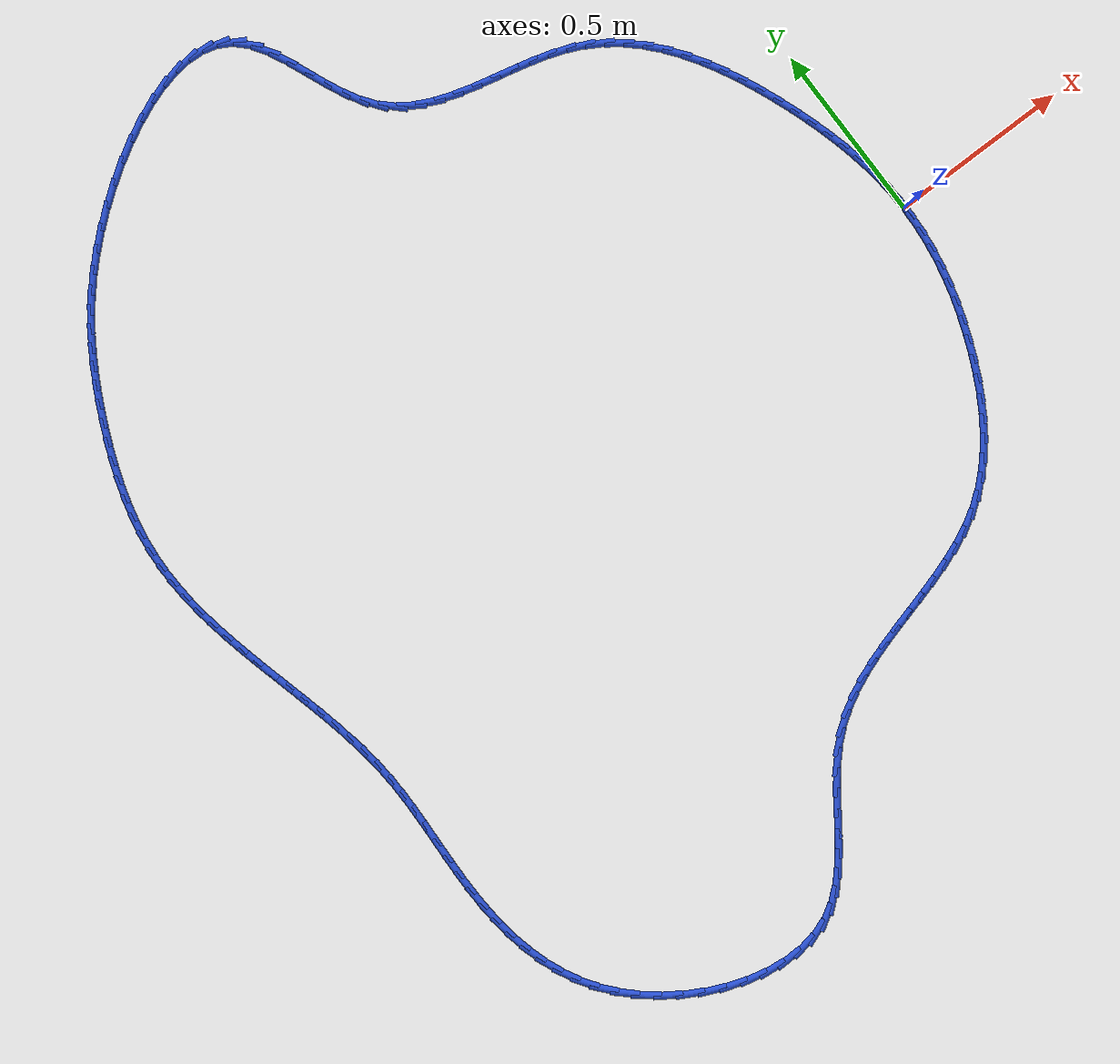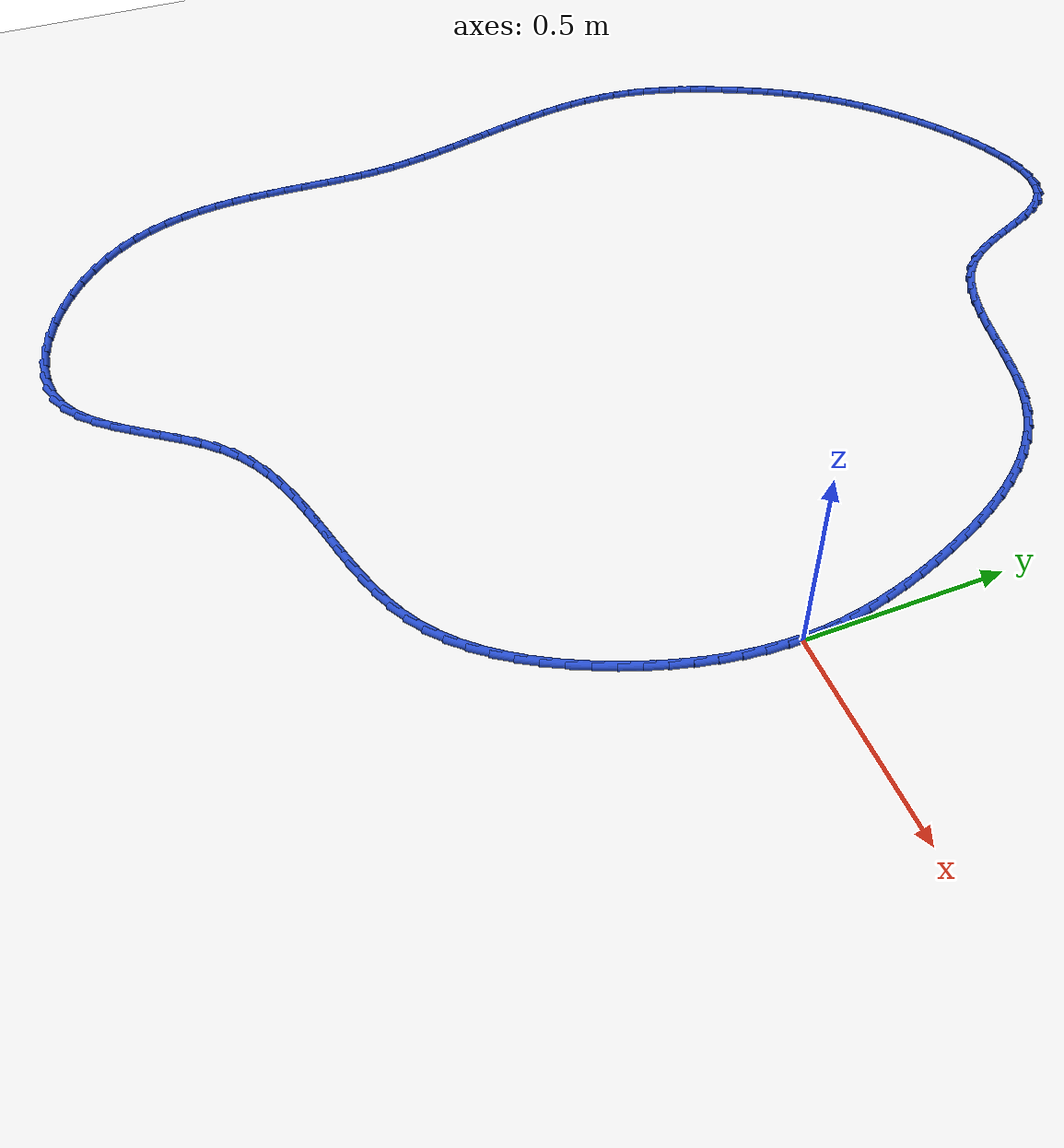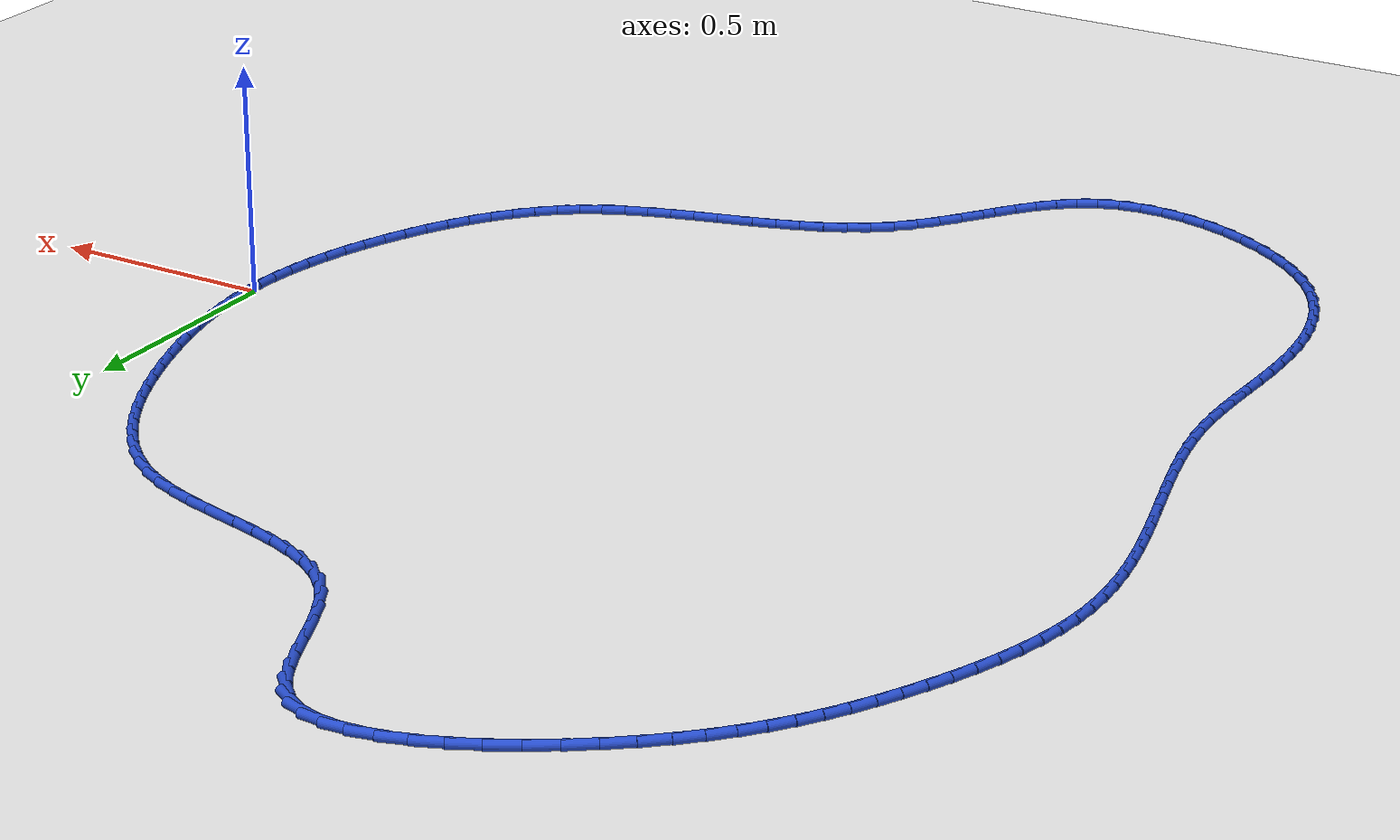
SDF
<sdf version="1.6">
 <world name="default">
  <light name="sun" type="directional">
   <pose>0 0 10 0 -0 0</pose>
   <diffuse>0.8 0.8 0.8 1</diffuse>
   <specular>0.2 0.2 0.2 1</specular>
   <attenuation>
    <range>1000</range>
    <constant>0.9</constant>
    <linear>0.01</linear>
    <quadratic>0.001</quadratic>
   </attenuation>
   <direction>-0.5 0.1 -0.9</direction>
  </light>
  <model name="ground_plane">
   <static>1</static>
   <link name="link">
    <collision name="collision">
     <geometry><plane><normal>0 0 1</normal><size>100 100</size></plane></geometry>
     <surface><friction><ode><mu>100</mu><mu2>50</mu2></ode></friction></surface>
    </collision>
    <visual name="visual">
     <cast_shadows>0</cast_shadows>
     <geometry><plane><normal>0 0 1</normal><size>100 100</size></plane></geometry>
     <material>
      <script><uri>file://media/materials/scripts/gazebo.material</uri><name>Gazebo/WhiteGlow</name></script>
     </material>
    </visual>
   </link>
  </model>
  <gravity>0 0 -9.8</gravity>
  <magnetic_field>6e-06 2.3e-05 -4.2e-05</magnetic_field>
  <atmosphere type="adiabatic"/>
  <physics name="default_physics" default="0" type="ode">
   <max_step_size>0.001</max_step_size>
   <real_time_factor>1</real_time_factor>
   <real_time_update_rate>1000</real_time_update_rate>
  </physics>
  <scene><ambient>0.4 0.4 0.4 1</ambient><background>0.7 0.7 0.7 1</background><shadows>1</shadows></scene>
  <spherical_coordinates>
   <surface_model>EARTH_WGS84</surface_model>
   <latitude_deg>0</latitude_deg>
   <longitude_deg>0</longitude_deg>
   <elevation>0</elevation>
   <heading_deg>0</heading_deg>
  </spherical_coordinates>
  <model name="line">
   <link name="link_0">
    <pose>2.0816681711721685e-17 5.551115123125783e-17 0.01 0 1.57 -1.5330412168781087</pose>
    <collision name="collision">
     <geometry><cylinder><radius>0.01</radius><length>0.08</length></cylinder></geometry>
    </collision>
    <visual name="visual">
     <material>
      <script><name>Gazebo/Blue</name><uri>file://media/materials/scripts/gazebo.material</uri></script>
     </material>
     <geometry><cylinder><radius>0.01</radius><length>0.08</length></cylinder></geometry>
    </visual>
   </link>
   <link name="link_1">
    <pose>-0.0019267832978807043 0.05100945819266871 0.01 0 1.57 -1.4757168661922142</pose>
    <collision name="collision">
     <geometry><cylinder><radius>0.01</radius><length>0.08</length></cylinder></geometry>
    </collision>
    <visual name="visual">
     <material>
      <script><name>Gazebo/Blue</name><uri>file://media/materials/scripts/gazebo.material</uri></script>
     </material>
     <geometry><cylinder><radius>0.01</radius><length>0.08</length></cylinder></geometry>
    </visual>
   </link>
   <link name="link_2">
    <pose>-0.006780246610819949 0.10190193475541207 0.01 0 1.57 -1.4226484117235143</pose>
    <collision name="collision">
     <geometry><cylinder><radius>0.01</radius><length>0.08</length></cylinder></geometry>
    </collision>
    <visual name="visual">
     <material>
      <script><name>Gazebo/Blue</name><uri>file://media/materials/scripts/gazebo.material</uri></script>
     </material>
     <geometry><cylinder><radius>0.01</radius><length>0.08</length></cylinder></geometry>
    </visual>
   </link>
   <link name="link_3">
    <pose>-0.014361618773334023 0.15270134025614557 0.01 0 1.57 -1.374074464920237</pose>
    <collision name="collision">
     <geometry><cylinder><radius>0.01</radius><length>0.08</length></cylinder></geometry>
    </collision>
    <visual name="visual">
     <material>
      <script><name>Gazebo/Blue</name><uri>file://media/materials/scripts/gazebo.material</uri></script>
     </material>
     <geometry><cylinder><radius>0.01</radius><length>0.08</length></cylinder></geometry>
    </visual>
   </link>
   <link name="link_4">
    <pose>-0.02447212861993922 0.20343158526278443 0.01 0 1.57 -1.3301000333956121</pose>
    <collision name="collision">
     <geometry><cylinder><radius>0.01</radius><length>0.08</length></cylinder></geometry>
    </collision>
    <visual name="visual">
     <material>
      <script><name>Gazebo/Blue</name><uri>file://media/materials/scripts/gazebo.material</uri></script>
     </material>
     <geometry><cylinder><radius>0.01</radius><length>0.08</length></cylinder></geometry>
    </visual>
   </link>
   <link name="link_5">
    <pose>-0.036913004985151834 0.254116580343244 0.01 0 1.57 -1.2907248943532754</pose>
    <collision name="collision">
     <geometry><cylinder><radius>0.01</radius><length>0.08</length></cylinder></geometry>
    </collision>
    <visual name="visual">
     <material>
      <script><name>Gazebo/Blue</name><uri>file://media/materials/scripts/gazebo.material</uri></script>
     </material>
     <geometry><cylinder><radius>0.01</radius><length>0.08</length></cylinder></geometry>
    </visual>
   </link>
   <link name="link_6">
    <pose>-0.05148547670348817 0.30478023606543964 0.01 0 1.57 -1.255872444186396</pose>
    <collision name="collision">
     <geometry><cylinder><radius>0.01</radius><length>0.08</length></cylinder></geometry>
    </collision>
    <visual name="visual">
     <material>
      <script><name>Gazebo/Blue</name><uri>file://media/materials/scripts/gazebo.material</uri></script>
     </material>
     <geometry><cylinder><radius>0.01</radius><length>0.08</length></cylinder></geometry>
    </visual>
   </link>
   <link name="link_7">
    <pose>-0.06799077260946451 0.35544646299728655 0.01 0 1.57 -1.2254158493264087</pose>
    <collision name="collision">
     <geometry><cylinder><radius>0.01</radius><length>0.08</length></cylinder></geometry>
    </collision>
    <visual name="visual">
     <material>
      <script><name>Gazebo/Blue</name><uri>file://media/materials/scripts/gazebo.material</uri></script>
     </material>
     <geometry><cylinder><radius>0.01</radius><length>0.08</length></cylinder></geometry>
    </visual>
   </link>
   <link name="link_8">
    <pose>-0.0862301215375972 0.4061391717067002 0.01 0 1.57 -1.1976445312591981</pose>
    <collision name="collision">
     <geometry><cylinder><radius>0.01</radius><length>0.08</length></cylinder></geometry>
    </collision>
    <visual name="visual">
     <material>
      <script><name>Gazebo/Blue</name><uri>file://media/materials/scripts/gazebo.material</uri></script>
     </material>
     <geometry><cylinder><radius>0.01</radius><length>0.08</length></cylinder></geometry>
    </visual>
   </link>
   <link name="link_9">
    <pose>-0.10606490799226363 0.4568035724961708 0.01 0 1.57 -1.1658548527337567</pose>
    <collision name="collision">
     <geometry><cylinder><radius>0.01</radius><length>0.08</length></cylinder></geometry>
    </collision>
    <visual name="visual">
     <material>
      <script><name>Gazebo/Blue</name><uri>file://media/materials/scripts/gazebo.material</uri></script>
     </material>
     <geometry><cylinder><radius>0.01</radius><length>0.08</length></cylinder></geometry>
    </visual>
   </link>
   <link name="link_10">
    <pose>-0.1276057963725649 0.5070587485728495 0.01 0 1.57 -1.1279025546585217</pose>
    <collision name="collision">
     <geometry><cylinder><radius>0.01</radius><length>0.08</length></cylinder></geometry>
    </collision>
    <visual name="visual">
     <material>
      <script><name>Gazebo/Blue</name><uri>file://media/materials/scripts/gazebo.material</uri></script>
     </material>
     <geometry><cylinder><radius>0.01</radius><length>0.08</length></cylinder></geometry>
    </visual>
   </link>
   <link name="link_11">
    <pose>-0.15102801265810506 0.5564393187279231 0.01 0 1.57 -1.083157277274956</pose>
    <collision name="collision">
     <geometry><cylinder><radius>0.01</radius><length>0.08</length></cylinder></geometry>
    </collision>
    <visual name="visual">
     <material>
      <script><name>Gazebo/Blue</name><uri>file://media/materials/scripts/gazebo.material</uri></script>
     </material>
     <geometry><cylinder><radius>0.01</radius><length>0.08</length></cylinder></geometry>
    </visual>
   </link>
   <link name="link_12">
    <pose>-0.17650678293041266 0.6044799016192317 0.01 0 1.57 -1.0308632642735505</pose>
    <collision name="collision">
     <geometry><cylinder><radius>0.01</radius><length>0.08</length></cylinder></geometry>
    </collision>
    <visual name="visual">
     <material>
      <script><name>Gazebo/Blue</name><uri>file://media/materials/scripts/gazebo.material</uri></script>
     </material>
     <geometry><cylinder><radius>0.01</radius><length>0.08</length></cylinder></geometry>
    </visual>
   </link>
   <link name="link_13">
    <pose>-0.2042173332710161 0.6507151159046158 0.01 0 1.57 -0.9701791857934083</pose>
    <collision name="collision">
     <geometry><cylinder><radius>0.01</radius><length>0.08</length></cylinder></geometry>
    </collision>
    <visual name="visual">
     <material>
      <script><name>Gazebo/Blue</name><uri>file://media/materials/scripts/gazebo.material</uri></script>
     </material>
     <geometry><cylinder><radius>0.01</radius><length>0.08</length></cylinder></geometry>
    </visual>
   </link>
   <link name="link_14">
    <pose>-0.2343348897614441 0.6946795802419162 0.01 0 1.57 -0.9002530958229978</pose>
    <collision name="collision">
     <geometry><cylinder><radius>0.01</radius><length>0.08</length></cylinder></geometry>
    </collision>
    <visual name="visual">
     <material>
      <script><name>Gazebo/Blue</name><uri>file://media/materials/scripts/gazebo.material</uri></script>
     </material>
     <geometry><cylinder><radius>0.01</radius><length>0.08</length></cylinder></geometry>
    </visual>
   </link>
   <link name="link_15">
    <pose>-0.26703467848322504 0.735907913288973 0.01 0 1.57 -0.8203516836143352</pose>
    <collision name="collision">
     <geometry><cylinder><radius>0.01</radius><length>0.08</length></cylinder></geometry>
    </collision>
    <visual name="visual">
     <material>
      <script><name>Gazebo/Blue</name><uri>file://media/materials/scripts/gazebo.material</uri></script>
     </material>
     <geometry><cylinder><radius>0.01</radius><length>0.08</length></cylinder></geometry>
    </visual>
   </link>
   <link name="link_16">
    <pose>-0.30249192551788756 0.773934733703627 0.01 0 1.57 -0.7300593564254582</pose>
    <collision name="collision">
     <geometry><cylinder><radius>0.01</radius><length>0.08</length></cylinder></geometry>
    </collision>
    <visual name="visual">
     <material>
      <script><name>Gazebo/Blue</name><uri>file://media/materials/scripts/gazebo.material</uri></script>
     </material>
     <geometry><cylinder><radius>0.01</radius><length>0.08</length></cylinder></geometry>
    </visual>
   </link>
   <link name="link_17">
    <pose>-0.34088185694696016 0.8082946601437184 0.01 0 1.57 -0.6295429983004225</pose>
    <collision name="collision">
     <geometry><cylinder><radius>0.01</radius><length>0.08</length></cylinder></geometry>
    </collision>
    <visual name="visual">
     <material>
      <script><name>Gazebo/Blue</name><uri>file://media/materials/scripts/gazebo.material</uri></script>
     </material>
     <geometry><cylinder><radius>0.01</radius><length>0.08</length></cylinder></geometry>
    </visual>
   </link>
   <link name="link_18">
    <pose>-0.3823796988519716 0.8385223112670882 0.01 0 1.57 -0.519833749858481</pose>
    <collision name="collision">
     <geometry><cylinder><radius>0.01</radius><length>0.08</length></cylinder></geometry>
    </collision>
    <visual name="visual">
     <material>
      <script><name>Gazebo/Blue</name><uri>file://media/materials/scripts/gazebo.material</uri></script>
     </material>
     <geometry><cylinder><radius>0.01</radius><length>0.08</length></cylinder></geometry>
    </visual>
   </link>
   <link name="link_19">
    <pose>-0.42716067731445007 0.8641523057315761 0.01 0 1.57 -0.40893463788574597</pose>
    <collision name="collision">
     <geometry><cylinder><radius>0.01</radius><length>0.08</length></cylinder></geometry>
    </collision>
    <visual name="visual">
     <material>
      <script><name>Gazebo/Blue</name><uri>file://media/materials/scripts/gazebo.material</uri></script>
     </material>
     <geometry><cylinder><radius>0.01</radius><length>0.08</length></cylinder></geometry>
    </visual>
   </link>
   <link name="link_20">
    <pose>-0.47523321694559 0.8849852703661415 0.01 0 1.57 -0.322410514022538</pose>
    <collision name="collision">
     <geometry><cylinder><radius>0.01</radius><length>0.08</length></cylinder></geometry>
    </collision>
    <visual name="visual">
     <material>
      <script><name>Gazebo/Blue</name><uri>file://media/materials/scripts/gazebo.material</uri></script>
     </material>
     <geometry><cylinder><radius>0.01</radius><length>0.08</length></cylinder></geometry>
    </visual>
   </link>
   <link name="link_21">
    <pose>-0.5259186442336489 0.9019175880185308 0.01 0 1.57 -0.2646112176032231</pose>
    <collision name="collision">
     <geometry><cylinder><radius>0.01</radius><length>0.08</length></cylinder></geometry>
    </collision>
    <visual name="visual">
     <material>
      <script><name>Gazebo/Blue</name><uri>file://media/materials/scripts/gazebo.material</uri></script>
     </material>
     <geometry><cylinder><radius>0.01</radius><length>0.08</length></cylinder></geometry>
    </visual>
   </link>
   <link name="link_22">
    <pose>-0.5783613907009115 0.9161277464021355 0.01 0 1.57 -0.23312956437793111</pose>
    <collision name="collision">
     <geometry><cylinder><radius>0.01</radius><length>0.08</length></cylinder></geometry>
    </collision>
    <visual name="visual">
     <material>
      <script><name>Gazebo/Blue</name><uri>file://media/materials/scripts/gazebo.material</uri></script>
     </material>
     <geometry><cylinder><radius>0.01</radius><length>0.08</length></cylinder></geometry>
    </visual>
   </link>
   <link name="link_23">
    <pose>-0.6317058877083502 0.9287942334876049 0.01 0 1.57 -0.22644988240983738</pose>
    <collision name="collision">
     <geometry><cylinder><radius>0.01</radius><length>0.08</length></cylinder></geometry>
    </collision>
    <visual name="visual">
     <material>
      <script><name>Gazebo/Blue</name><uri>file://media/materials/scripts/gazebo.material</uri></script>
     </material>
     <geometry><cylinder><radius>0.01</radius><length>0.08</length></cylinder></geometry>
    </visual>
   </link>
   <link name="link_24">
    <pose>-0.6850965666169365 0.9410955372455871 0.01 0 1.57 -0.24442881226614102</pose>
    <collision name="collision">
     <geometry><cylinder><radius>0.01</radius><length>0.08</length></cylinder></geometry>
    </collision>
    <visual name="visual">
     <material>
      <script><name>Gazebo/Blue</name><uri>file://media/materials/scripts/gazebo.material</uri></script>
     </material>
     <geometry><cylinder><radius>0.01</radius><length>0.08</length></cylinder></geometry>
    </visual>
   </link>
   <link name="link_25">
    <pose>-0.7376778587876425 0.9542101456467309 0.01 0 1.57 -0.2884179342264862</pose>
    <collision name="collision">
     <geometry><cylinder><radius>0.01</radius><length>0.08</length></cylinder></geometry>
    </collision>
    <visual name="visual">
     <material>
      <script><name>Gazebo/Blue</name><uri>file://media/materials/scripts/gazebo.material</uri></script>
     </material>
     <geometry><cylinder><radius>0.01</radius><length>0.08</length></cylinder></geometry>
    </visual>
   </link>
   <link name="link_26">
    <pose>-0.7885941955814394 0.9693165466616845 0.01 0 1.57 -0.3610919839227639</pose>
    <collision name="collision">
     <geometry><cylinder><radius>0.01</radius><length>0.08</length></cylinder></geometry>
    </collision>
    <visual name="visual">
     <material>
      <script><name>Gazebo/Blue</name><uri>file://media/materials/scripts/gazebo.material</uri></script>
     </material>
     <geometry><cylinder><radius>0.01</radius><length>0.08</length></cylinder></geometry>
    </visual>
   </link>
   <link name="link_27">
    <pose>-0.8369900083592996 0.9875932282610964 0.01 0 1.57 -0.46569953361430766</pose>
    <collision name="collision">
     <geometry><cylinder><radius>0.01</radius><length>0.08</length></cylinder></geometry>
    </collision>
    <visual name="visual">
     <material>
      <script><name>Gazebo/Blue</name><uri>file://media/materials/scripts/gazebo.material</uri></script>
     </material>
     <geometry><cylinder><radius>0.01</radius><length>0.08</length></cylinder></geometry>
    </visual>
   </link>
   <link name="link_28">
    <pose>-0.8820097284821946 1.0102186784156155 0.01 0 1.57 -0.6041315512340685</pose>
    <collision name="collision">
     <geometry><cylinder><radius>0.01</radius><length>0.08</length></cylinder></geometry>
    </collision>
    <visual name="visual">
     <material>
      <script><name>Gazebo/Blue</name><uri>file://media/materials/scripts/gazebo.material</uri></script>
     </material>
     <geometry><cylinder><radius>0.01</radius><length>0.08</length></cylinder></geometry>
    </visual>
   </link>
   <link name="link_29">
    <pose>-0.9227977873110964 1.03837138509589 0.01 0 1.57 -0.7734601490006462</pose>
    <collision name="collision">
     <geometry><cylinder><radius>0.01</radius><length>0.08</length></cylinder></geometry>
    </collision>
    <visual name="visual">
     <material>
      <script><name>Gazebo/Blue</name><uri>file://media/materials/scripts/gazebo.material</uri></script>
     </material>
     <geometry><cylinder><radius>0.01</radius><length>0.08</length></cylinder></geometry>
    </visual>
   </link>
   <link name="link_30">
    <pose>-0.9584986162069769 1.073229836272569 0.01 0 1.57 -0.9501460204746253</pose>
    <collision name="collision">
     <geometry><cylinder><radius>0.01</radius><length>0.08</length></cylinder></geometry>
    </collision>
    <visual name="visual">
     <material>
      <script><name>Gazebo/Blue</name><uri>file://media/materials/scripts/gazebo.material</uri></script>
     </material>
     <geometry><cylinder><radius>0.01</radius><length>0.08</length></cylinder></geometry>
    </visual>
   </link>
   <link name="link_31">
    <pose>-0.9886439385506127 1.1153975423496196 0.01 0 1.57 -1.0762772994941054</pose>
    <collision name="collision">
     <geometry><cylinder><radius>0.01</radius><length>0.08</length></cylinder></geometry>
    </collision>
    <visual name="visual">
     <material>
      <script><name>Gazebo/Blue</name><uri>file://media/materials/scripts/gazebo.material</uri></script>
     </material>
     <geometry><cylinder><radius>0.01</radius><length>0.08</length></cylinder></geometry>
    </visual>
   </link>
   <link name="link_32">
    <pose>-1.014366243199333 1.1631015014574133 0.01 0 1.57 -1.1485752905730249</pose>
    <collision name="collision">
     <geometry><cylinder><radius>0.01</radius><length>0.08</length></cylinder></geometry>
    </collision>
    <visual name="visual">
     <material>
      <script><name>Gazebo/Blue</name><uri>file://media/materials/scripts/gazebo.material</uri></script>
     </material>
     <geometry><cylinder><radius>0.01</radius><length>0.08</length></cylinder></geometry>
    </visual>
   </link>
   <link name="link_33">
    <pose>-1.037211536472663 1.2139547996082418 0.01 0 1.57 -1.175877479725167</pose>
    <collision name="collision">
     <geometry><cylinder><radius>0.01</radius><length>0.08</length></cylinder></geometry>
    </collision>
    <visual name="visual">
     <material>
      <script><name>Gazebo/Blue</name><uri>file://media/materials/scripts/gazebo.material</uri></script>
     </material>
     <geometry><cylinder><radius>0.01</radius><length>0.08</length></cylinder></geometry>
    </visual>
   </link>
   <link name="link_34">
    <pose>-1.0587258252114158 1.2655705220404894 0.01 0 1.57 -1.160770388033132</pose>
    <collision name="collision">
     <geometry><cylinder><radius>0.01</radius><length>0.08</length></cylinder></geometry>
    </collision>
    <visual name="visual">
     <material>
      <script><name>Gazebo/Blue</name><uri>file://media/materials/scripts/gazebo.material</uri></script>
     </material>
     <geometry><cylinder><radius>0.01</radius><length>0.08</length></cylinder></geometry>
    </visual>
   </link>
   <link name="link_35">
    <pose>-1.0804551162564031 1.3155617539925404 0.01 0 1.57 -1.098480471711266</pose>
    <collision name="collision">
     <geometry><cylinder><radius>0.01</radius><length>0.08</length></cylinder></geometry>
    </collision>
    <visual name="visual">
     <material>
      <script><name>Gazebo/Blue</name><uri>file://media/materials/scripts/gazebo.material</uri></script>
     </material>
     <geometry><cylinder><radius>0.01</radius><length>0.08</length></cylinder></geometry>
    </visual>
   </link>
   <link name="link_36">
    <pose>-1.1039454164484377 1.361541580702779 0.01 0 1.57 -0.9756629332985222</pose>
    <collision name="collision">
     <geometry><cylinder><radius>0.01</radius><length>0.08</length></cylinder></geometry>
    </collision>
    <visual name="visual">
     <material>
      <script><name>Gazebo/Blue</name><uri>file://media/materials/scripts/gazebo.material</uri></script>
     </material>
     <geometry><cylinder><radius>0.01</radius><length>0.08</length></cylinder></geometry>
    </visual>
   </link>
   <link name="link_37">
    <pose>-1.1307427326283317 1.4011230874095895 0.01 0 1.57 -0.7718781270696224</pose>
    <collision name="collision">
     <geometry><cylinder><radius>0.01</radius><length>0.08</length></cylinder></geometry>
    </collision>
    <visual name="visual">
     <material>
      <script><name>Gazebo/Blue</name><uri>file://media/materials/scripts/gazebo.material</uri></script>
     </material>
     <geometry><cylinder><radius>0.01</radius><length>0.08</length></cylinder></geometry>
    </visual>
   </link>
   <link name="link_38">
    <pose>-1.1623889469960382 1.4319249500600415 0.01 0 1.57 -0.5040491336817796</pose>
    <collision name="collision">
     <geometry><cylinder><radius>0.01</radius><length>0.08</length></cylinder></geometry>
    </collision>
    <visual name="visual">
     <material>
      <script><name>Gazebo/Blue</name><uri>file://media/materials/scripts/gazebo.material</uri></script>
     </material>
     <geometry><cylinder><radius>0.01</radius><length>0.08</length></cylinder></geometry>
    </visual>
   </link>
   <link name="link_39">
    <pose>-1.199723672049727 1.4525177299784982 0.01 0 1.57 -0.2534060157428631</pose>
    <collision name="collision">
     <geometry><cylinder><radius>0.01</radius><length>0.08</length></cylinder></geometry>
    </collision>
    <visual name="visual">
     <material>
      <script><name>Gazebo/Blue</name><uri>file://media/materials/scripts/gazebo.material</uri></script>
     </material>
     <geometry><cylinder><radius>0.01</radius><length>0.08</length></cylinder></geometry>
    </visual>
   </link>
   <link name="link_40">
    <pose>-1.2420967896434874 1.463491230972106 0.01 0 1.57 -0.047241670514613025</pose>
    <collision name="collision">
     <geometry><cylinder><radius>0.01</radius><length>0.08</length></cylinder></geometry>
    </collision>
    <visual name="visual">
     <material>
      <script><name>Gazebo/Blue</name><uri>file://media/materials/scripts/gazebo.material</uri></script>
     </material>
     <geometry><cylinder><radius>0.01</radius><length>0.08</length></cylinder></geometry>
    </visual>
   </link>
   <link name="link_41">
    <pose>-1.2886680470303864 1.4656929731441437 0.01 0 1.57 0.11411441910101199</pose>
    <collision name="collision">
     <geometry><cylinder><radius>0.01</radius><length>0.08</length></cylinder></geometry>
    </collision>
    <visual name="visual">
     <material>
      <script><name>Gazebo/Blue</name><uri>file://media/materials/scripts/gazebo.material</uri></script>
     </material>
     <geometry><cylinder><radius>0.01</radius><length>0.08</length></cylinder></geometry>
    </visual>
   </link>
   <link name="link_42">
    <pose>-1.3385971914634907 1.4599704765978907 0.01 0 1.57 0.23936329155781605</pose>
    <collision name="collision">
     <geometry><cylinder><radius>0.01</radius><length>0.08</length></cylinder></geometry>
    </collision>
    <visual name="visual">
     <material>
      <script><name>Gazebo/Blue</name><uri>file://media/materials/scripts/gazebo.material</uri></script>
     </material>
     <geometry><cylinder><radius>0.01</radius><length>0.08</length></cylinder></geometry>
    </visual>
   </link>
   <link name="link_43">
    <pose>-1.391043970195867 1.4471712614366257 0.01 0 1.57 0.33807251238435</pose>
    <collision name="collision">
     <geometry><cylinder><radius>0.01</radius><length>0.08</length></cylinder></geometry>
    </collision>
    <visual name="visual">
     <material>
      <script><name>Gazebo/Blue</name><uri>file://media/materials/scripts/gazebo.material</uri></script>
     </material>
     <geometry><cylinder><radius>0.01</radius><length>0.08</length></cylinder></geometry>
    </visual>
   </link>
   <link name="link_44">
    <pose>-1.445168130480584 1.4281428477636284 0.01 0 1.57 0.41796376953160397</pose>
    <collision name="collision">
     <geometry><cylinder><radius>0.01</radius><length>0.08</length></cylinder></geometry>
    </collision>
    <visual name="visual">
     <material>
      <script><name>Gazebo/Blue</name><uri>file://media/materials/scripts/gazebo.material</uri></script>
     </material>
     <geometry><cylinder><radius>0.01</radius><length>0.08</length></cylinder></geometry>
    </visual>
   </link>
   <link name="link_45">
    <pose>-1.5001294195707089 1.4037327556821773 0.01 0 1.57 0.48474719495105406</pose>
    <collision name="collision">
     <geometry><cylinder><radius>0.01</radius><length>0.08</length></cylinder></geometry>
    </collision>
    <visual name="visual">
     <material>
      <script><name>Gazebo/Blue</name><uri>file://media/materials/scripts/gazebo.material</uri></script>
     </material>
     <geometry><cylinder><radius>0.01</radius><length>0.08</length></cylinder></geometry>
    </visual>
   </link>
   <link name="link_46">
    <pose>-1.5550875847193069 1.3747885052955513 0.01 0 1.57 0.5426180068361647</pose>
    <collision name="collision">
     <geometry><cylinder><radius>0.01</radius><length>0.08</length></cylinder></geometry>
    </collision>
    <visual name="visual">
     <material>
      <script><name>Gazebo/Blue</name><uri>file://media/materials/scripts/gazebo.material</uri></script>
     </material>
     <geometry><cylinder><radius>0.01</radius><length>0.08</length></cylinder></geometry>
    </visual>
   </link>
   <link name="link_47">
    <pose>-1.6092023731794471 1.3421576167070306 0.01 0 1.57 0.5947837218043405</pose>
    <collision name="collision">
     <geometry><cylinder><radius>0.01</radius><length>0.08</length></cylinder></geometry>
    </collision>
    <visual name="visual">
     <material>
      <script><name>Gazebo/Blue</name><uri>file://media/materials/scripts/gazebo.material</uri></script>
     </material>
     <geometry><cylinder><radius>0.01</radius><length>0.08</length></cylinder></geometry>
    </visual>
   </link>
   <link name="link_48">
    <pose>-1.6616335322041962 1.3066876100198939 0.01 0 1.57 0.6439004121174262</pose>
    <collision name="collision">
     <geometry><cylinder><radius>0.01</radius><length>0.08</length></cylinder></geometry>
    </collision>
    <visual name="visual">
     <material>
      <script><name>Gazebo/Blue</name><uri>file://media/materials/scripts/gazebo.material</uri></script>
     </material>
     <geometry><cylinder><radius>0.01</radius><length>0.08</length></cylinder></geometry>
    </visual>
   </link>
   <link name="link_49">
    <pose>-1.7115408090466215 1.2692260053374194 0.01 0 1.57 0.6924481186817071</pose>
    <collision name="collision">
     <geometry><cylinder><radius>0.01</radius><length>0.08</length></cylinder></geometry>
    </collision>
    <visual name="visual">
     <material>
      <script><name>Gazebo/Blue</name><uri>file://media/materials/scripts/gazebo.material</uri></script>
     </material>
     <geometry><cylinder><radius>0.01</radius><length>0.08</length></cylinder></geometry>
    </visual>
   </link>
   <link name="link_50">
    <pose>-1.7580839509597905 1.230620322762887 0.01 0 1.57 0.7428412917880801</pose>
    <collision name="collision">
     <geometry><cylinder><radius>0.01</radius><length>0.08</length></cylinder></geometry>
    </collision>
    <visual name="visual">
     <material>
      <script><name>Gazebo/Blue</name><uri>file://media/materials/scripts/gazebo.material</uri></script>
     </material>
     <geometry><cylinder><radius>0.01</radius><length>0.08</length></cylinder></geometry>
    </visual>
   </link>
   <link name="link_51">
    <pose>-1.8005897082279445 1.1915867218703458 0.01 0 1.57 0.7953144953668434</pose>
    <collision name="collision">
     <geometry><cylinder><radius>0.01</radius><length>0.08</length></cylinder></geometry>
    </collision>
    <visual name="visual">
     <material>
      <script><name>Gazebo/Blue</name><uri>file://media/materials/scripts/gazebo.material</uri></script>
     </material>
     <geometry><cylinder><radius>0.01</radius><length>0.08</length></cylinder></geometry>
    </visual>
   </link>
   <link name="link_52">
    <pose>-1.839212079004511 1.1521906691468031 0.01 0 1.57 0.8485511496075425</pose>
    <collision name="collision">
     <geometry><cylinder><radius>0.01</radius><length>0.08</length></cylinder></geometry>
    </collision>
    <visual name="visual">
     <material>
      <script><name>Gazebo/Blue</name><uri>file://media/materials/scripts/gazebo.material</uri></script>
     </material>
     <geometry><cylinder><radius>0.01</radius><length>0.08</length></cylinder></geometry>
    </visual>
   </link>
   <link name="link_53">
    <pose>-1.8743607388020056 1.1122965214768503 0.01 0 1.57 0.9011562233517446</pose>
    <collision name="collision">
     <geometry><cylinder><radius>0.01</radius><length>0.08</length></cylinder></geometry>
    </collision>
    <visual name="visual">
     <material>
      <script><name>Gazebo/Blue</name><uri>file://media/materials/scripts/gazebo.material</uri></script>
     </material>
     <geometry><cylinder><radius>0.01</radius><length>0.08</length></cylinder></geometry>
    </visual>
   </link>
   <link name="link_54">
    <pose>-1.9064454378836169 1.071768576948012 0.01 0 1.57 0.951632944414689</pose>
    <collision name="collision">
     <geometry><cylinder><radius>0.01</radius><length>0.08</length></cylinder></geometry>
    </collision>
    <visual name="visual">
     <material>
      <script><name>Gazebo/Blue</name><uri>file://media/materials/scripts/gazebo.material</uri></script>
     </material>
     <geometry><cylinder><radius>0.01</radius><length>0.08</length></cylinder></geometry>
    </visual>
   </link>
   <link name="link_55">
    <pose>-1.9358759265125334 1.0304711336478165 0.01 0 1.57 0.9985245662462175</pose>
    <collision name="collision">
     <geometry><cylinder><radius>0.01</radius><length>0.08</length></cylinder></geometry>
    </collision>
    <visual name="visual">
     <material>
      <script><name>Gazebo/Blue</name><uri>file://media/materials/scripts/gazebo.material</uri></script>
     </material>
     <geometry><cylinder><radius>0.01</radius><length>0.08</length></cylinder></geometry>
    </visual>
   </link>
   <link name="link_56">
    <pose>-1.9630619549519448 0.9882684896637889 0.01 0 1.57 1.0405521005994913</pose>
    <collision name="collision">
     <geometry><cylinder><radius>0.01</radius><length>0.08</length></cylinder></geometry>
    </collision>
    <visual name="visual">
     <material>
      <script><name>Gazebo/Blue</name><uri>file://media/materials/scripts/gazebo.material</uri></script>
     </material>
     <geometry><cylinder><radius>0.01</radius><length>0.08</length></cylinder></geometry>
    </visual>
   </link>
   <link name="link_57">
    <pose>-1.9884132734650395 0.9450249430834553 0.01 0 1.57 1.0767185622705102</pose>
    <collision name="collision">
     <geometry><cylinder><radius>0.01</radius><length>0.08</length></cylinder></geometry>
    </collision>
    <visual name="visual">
     <material>
      <script><name>Gazebo/Blue</name><uri>file://media/materials/scripts/gazebo.material</uri></script>
     </material>
     <geometry><cylinder><radius>0.01</radius><length>0.08</length></cylinder></geometry>
    </visual>
   </link>
   <link name="link_58">
    <pose>-2.0123396323150073 0.9006047919943416 0.01 0 1.57 1.1065300352826224</pose>
    <collision name="collision">
     <geometry><cylinder><radius>0.01</radius><length>0.08</length></cylinder></geometry>
    </collision>
    <visual name="visual">
     <material>
      <script><name>Gazebo/Blue</name><uri>file://media/materials/scripts/gazebo.material</uri></script>
     </material>
     <geometry><cylinder><radius>0.01</radius><length>0.08</length></cylinder></geometry>
    </visual>
   </link>
   <link name="link_59">
    <pose>-2.0352388207915904 0.8548771641449224 0.01 0 1.57 1.134573228270334</pose>
    <collision name="collision">
     <geometry><cylinder><radius>0.01</radius><length>0.08</length></cylinder></geometry>
    </collision>
    <visual name="visual">
     <material>
      <script><name>Gazebo/Blue</name><uri>file://media/materials/scripts/gazebo.material</uri></script>
     </material>
     <geometry><cylinder><radius>0.01</radius><length>0.08</length></cylinder></geometry>
    </visual>
   </link>
   <link name="link_60">
    <pose>-2.05716096362098 0.807851568998694 0.01 0 1.57 1.166539977617122</pose>
    <collision name="collision">
     <geometry><cylinder><radius>0.01</radius><length>0.08</length></cylinder></geometry>
    </collision>
    <visual name="visual">
     <material>
      <script><name>Gazebo/Blue</name><uri>file://media/materials/scripts/gazebo.material</uri></script>
     </material>
     <geometry><cylinder><radius>0.01</radius><length>0.08</length></cylinder></geometry>
    </visual>
   </link>
   <link name="link_61">
    <pose>-2.077762679846535 0.7596964076877841 0.01 0 1.57 1.2031058721673062</pose>
    <collision name="collision">
     <geometry><cylinder><radius>0.01</radius><length>0.08</length></cylinder></geometry>
    </collision>
    <visual name="visual">
     <material>
      <script><name>Gazebo/Blue</name><uri>file://media/materials/scripts/gazebo.material</uri></script>
     </material>
     <geometry><cylinder><radius>0.01</radius><length>0.08</length></cylinder></geometry>
    </visual>
   </link>
   <link name="link_62">
    <pose>-2.0966794152020474 0.7105886308078588 0.01 0 1.57 1.244732987011108</pose>
    <collision name="collision">
     <geometry><cylinder><radius>0.01</radius><length>0.08</length></cylinder></geometry>
    </collision>
    <visual name="visual">
     <material>
      <script><name>Gazebo/Blue</name><uri>file://media/materials/scripts/gazebo.material</uri></script>
     </material>
     <geometry><cylinder><radius>0.01</radius><length>0.08</length></cylinder></geometry>
    </visual>
   </link>
   <link name="link_63">
    <pose>-2.113546615421306 0.6607051889545855 0.01 0 1.57 1.2919539699727254</pose>
    <collision name="collision">
     <geometry><cylinder><radius>0.01</radius><length>0.08</length></cylinder></geometry>
    </collision>
    <visual name="visual">
     <material>
      <script><name>Gazebo/Blue</name><uri>file://media/materials/scripts/gazebo.material</uri></script>
     </material>
     <geometry><cylinder><radius>0.01</radius><length>0.08</length></cylinder></geometry>
    </visual>
   </link>
   <link name="link_64">
    <pose>-2.127999726238101 0.6102230327236301 0.01 0 1.57 1.3453518433506855</pose>
    <collision name="collision">
     <geometry><cylinder><radius>0.01</radius><length>0.08</length></cylinder></geometry>
    </collision>
    <visual name="visual">
     <material>
      <script><name>Gazebo/Blue</name><uri>file://media/materials/scripts/gazebo.material</uri></script>
     </material>
     <geometry><cylinder><radius>0.01</radius><length>0.08</length></cylinder></geometry>
    </visual>
   </link>
   <link name="link_65">
    <pose>-2.139674193386225 0.5593191127106597 0.01 0 1.57 1.4055243800006232</pose>
    <collision name="collision">
     <geometry><cylinder><radius>0.01</radius><length>0.08</length></cylinder></geometry>
    </collision>
    <visual name="visual">
     <material>
      <script><name>Gazebo/Blue</name><uri>file://media/materials/scripts/gazebo.material</uri></script>
     </material>
     <geometry><cylinder><radius>0.01</radius><length>0.08</length></cylinder></geometry>
    </visual>
   </link>
   <link name="link_66">
    <pose>-2.148205462599466 0.5081703795113407 0.01 0 1.57 1.4728889256258975</pose>
    <collision name="collision">
     <geometry><cylinder><radius>0.01</radius><length>0.08</length></cylinder></geometry>
    </collision>
    <visual name="visual">
     <material>
      <script><name>Gazebo/Blue</name><uri>file://media/materials/scripts/gazebo.material</uri></script>
     </material>
     <geometry><cylinder><radius>0.01</radius><length>0.08</length></cylinder></geometry>
    </visual>
   </link>
   <link name="link_67">
    <pose>-2.1532362039150708 0.45695202099705917 0.01 0 1.57 1.541915040390049</pose>
    <collision name="collision">
     <geometry><cylinder><radius>0.01</radius><length>0.08</length></cylinder></geometry>
    </collision>
    <visual name="visual">
     <material>
      <script><name>Gazebo/Blue</name><uri>file://media/materials/scripts/gazebo.material</uri></script>
     </material>
     <geometry><cylinder><radius>0.01</radius><length>0.08</length></cylinder></geometry>
    </visual>
   </link>
   <link name="link_68">
    <pose>-2.154714973984759 0.4057645889492517 0.01 0 1.57 -1.5373398081538736</pose>
    <collision name="collision">
     <geometry><cylinder><radius>0.01</radius><length>0.08</length></cylinder></geometry>
    </collision>
    <visual name="visual">
     <material>
      <script><name>Gazebo/Blue</name><uri>file://media/materials/scripts/gazebo.material</uri></script>
     </material>
     <geometry><cylinder><radius>0.01</radius><length>0.08</length></cylinder></geometry>
    </visual>
   </link>
   <link name="link_69">
    <pose>-2.153002813381531 0.35460798940156985 0.01 0 1.57 -1.4827661530690768</pose>
    <collision name="collision">
     <geometry><cylinder><radius>0.01</radius><length>0.08</length></cylinder></geometry>
    </collision>
    <visual name="visual">
     <material>
      <script><name>Gazebo/Blue</name><uri>file://media/materials/scripts/gazebo.material</uri></script>
     </material>
     <geometry><cylinder><radius>0.01</radius><length>0.08</length></cylinder></geometry>
    </visual>
   </link>
   <link name="link_70">
    <pose>-2.1484899056481317 0.30347501752629247 0.01 0 1.57 -1.4361707752430863</pose>
    <collision name="collision">
     <geometry><cylinder><radius>0.01</radius><length>0.08</length></cylinder></geometry>
    </collision>
    <visual name="visual">
     <material>
      <script><name>Gazebo/Blue</name><uri>file://media/materials/scripts/gazebo.material</uri></script>
     </material>
     <geometry><cylinder><radius>0.01</radius><length>0.08</length></cylinder></geometry>
    </visual>
   </link>
   <link name="link_71">
    <pose>-2.141566434327305 0.25235846849569804 0.01 0 1.57 -1.3975493610285235</pose>
    <collision name="collision">
     <geometry><cylinder><radius>0.01</radius><length>0.08</length></cylinder></geometry>
    </collision>
    <visual name="visual">
     <material>
      <script><name>Gazebo/Blue</name><uri>file://media/materials/scripts/gazebo.material</uri></script>
     </material>
     <geometry><cylinder><radius>0.01</radius><length>0.08</length></cylinder></geometry>
    </visual>
   </link>
   <link name="link_72">
    <pose>-2.1326225829617957 0.20125113748206644 0.01 0 1.57 -1.3667683302339775</pose>
    <collision name="collision">
     <geometry><cylinder><radius>0.01</radius><length>0.08</length></cylinder></geometry>
    </collision>
    <visual name="visual">
     <material>
      <script><name>Gazebo/Blue</name><uri>file://media/materials/scripts/gazebo.material</uri></script>
     </material>
     <geometry><cylinder><radius>0.01</radius><length>0.08</length></cylinder></geometry>
    </visual>
   </link>
   <link name="link_73">
    <pose>-2.1220485350943483 0.15014581965767604 0.01 0 1.57 -1.3436384703742192</pose>
    <collision name="collision">
     <geometry><cylinder><radius>0.01</radius><length>0.08</length></cylinder></geometry>
    </collision>
    <visual name="visual">
     <material>
      <script><name>Gazebo/Blue</name><uri>file://media/materials/scripts/gazebo.material</uri></script>
     </material>
     <geometry><cylinder><radius>0.01</radius><length>0.08</length></cylinder></geometry>
    </visual>
   </link>
   <link name="link_74">
    <pose>-2.1102344742677084 0.09903531019480578 0.01 0 1.57 -1.3279697814138556</pose>
    <collision name="collision">
     <geometry><cylinder><radius>0.01</radius><length>0.08</length></cylinder></geometry>
    </collision>
    <visual name="visual">
     <material>
      <script><name>Gazebo/Blue</name><uri>file://media/materials/scripts/gazebo.material</uri></script>
     </material>
     <geometry><cylinder><radius>0.01</radius><length>0.08</length></cylinder></geometry>
    </visual>
   </link>
   <link name="link_75">
    <pose>-2.0975705840246195 0.04791240426573468 0.01 0 1.57 -1.3196088449746572</pose>
    <collision name="collision">
     <geometry><cylinder><radius>0.01</radius><length>0.08</length></cylinder></geometry>
    </collision>
    <visual name="visual">
     <material>
      <script><name>Gazebo/Blue</name><uri>file://media/materials/scripts/gazebo.material</uri></script>
     </material>
     <geometry><cylinder><radius>0.01</radius><length>0.08</length></cylinder></geometry>
    </visual>
   </link>
   <link name="link_76">
    <pose>-2.084447047907826 -0.0032301029572587847 0.01 0 1.57 -1.31846167300155</pose>
    <collision name="collision">
     <geometry><cylinder><radius>0.01</radius><length>0.08</length></cylinder></geometry>
    </collision>
    <visual name="visual">
     <material>
      <script><name>Gazebo/Blue</name><uri>file://media/materials/scripts/gazebo.material</uri></script>
     </material>
     <geometry><cylinder><radius>0.01</radius><length>0.08</length></cylinder></geometry>
    </visual>
   </link>
   <link name="link_77">
    <pose>-2.071254049460073 -0.054399416301895265 0.01 0 1.57 -1.3245048321381647</pose>
    <collision name="collision">
     <geometry><cylinder><radius>0.01</radius><length>0.08</length></cylinder></geometry>
    </collision>
    <visual name="visual">
     <material>
      <script><name>Gazebo/Blue</name><uri>file://media/materials/scripts/gazebo.material</uri></script>
     </material>
     <geometry><cylinder><radius>0.01</radius><length>0.08</length></cylinder></geometry>
    </visual>
   </link>
   <link name="link_78">
    <pose>-2.0583817722241053 -0.10560274059589497 0.01 0 1.57 -1.3377865852273478</pose>
    <collision name="collision">
     <geometry><cylinder><radius>0.01</radius><length>0.08</length></cylinder></geometry>
    </collision>
    <visual name="visual">
     <material>
      <script><name>Gazebo/Blue</name><uri>file://media/materials/scripts/gazebo.material</uri></script>
     </material>
     <geometry><cylinder><radius>0.01</radius><length>0.08</length></cylinder></geometry>
    </visual>
   </link>
   <link name="link_79">
    <pose>-2.0462203997426673 -0.15684728066698067 0.01 0 1.57 -1.3584183952032456</pose>
    <collision name="collision">
     <geometry><cylinder><radius>0.01</radius><length>0.08</length></cylinder></geometry>
    </collision>
    <visual name="visual">
     <material>
      <script><name>Gazebo/Blue</name><uri>file://media/materials/scripts/gazebo.material</uri></script>
     </material>
     <geometry><cylinder><radius>0.01</radius><length>0.08</length></cylinder></geometry>
    </visual>
   </link>
   <link name="link_80">
    <pose>-2.0351601155585035 -0.20814024134287168 0.01 0 1.57 -1.3865557244322242</pose>
    <collision name="collision">
     <geometry><cylinder><radius>0.01</radius><length>0.08</length></cylinder></geometry>
    </collision>
    <visual name="visual">
     <material>
      <script><name>Gazebo/Blue</name><uri>file://media/materials/scripts/gazebo.material</uri></script>
     </material>
     <geometry><cylinder><radius>0.01</radius><length>0.08</length></cylinder></geometry>
    </visual>
   </link>
   <link name="link_81">
    <pose>-2.0255911032143588 -0.25948882745129087 0.01 0 1.57 -1.4223659187849609</pose>
    <collision name="collision">
     <geometry><cylinder><radius>0.01</radius><length>0.08</length></cylinder></geometry>
    </collision>
    <visual name="visual">
     <material>
      <script><name>Gazebo/Blue</name><uri>file://media/materials/scripts/gazebo.material</uri></script>
     </material>
     <geometry><cylinder><radius>0.01</radius><length>0.08</length></cylinder></geometry>
    </visual>
   </link>
   <link name="link_82">
    <pose>-2.017903546252977 -0.3109002438199584 0.01 0 1.57 -1.4659805220283877</pose>
    <collision name="collision">
     <geometry><cylinder><radius>0.01</radius><length>0.08</length></cylinder></geometry>
    </collision>
    <visual name="visual">
     <material>
      <script><name>Gazebo/Blue</name><uri>file://media/materials/scripts/gazebo.material</uri></script>
     </material>
     <geometry><cylinder><radius>0.01</radius><length>0.08</length></cylinder></geometry>
    </visual>
   </link>
   <link name="link_83">
    <pose>-2.012487628217104 -0.36238169527659453 0.01 0 1.57 -1.5161075767296883</pose>
    <collision name="collision">
     <geometry><cylinder><radius>0.01</radius><length>0.08</length></cylinder></geometry>
    </collision>
    <visual name="visual">
     <material>
      <script><name>Gazebo/Blue</name><uri>file://media/materials/scripts/gazebo.material</uri></script>
     </material>
     <geometry><cylinder><radius>0.01</radius><length>0.08</length></cylinder></geometry>
    </visual>
   </link>
   <link name="link_84">
    <pose>-2.00966514301978 -0.4139402104610438 0.01 0 1.57 -1.5603521216147471</pose>
    <collision name="collision">
     <geometry><cylinder><radius>0.01</radius><length>0.08</length></cylinder></geometry>
    </collision>
    <visual name="visual">
     <material>
      <script><name>Gazebo/Blue</name><uri>file://media/materials/scripts/gazebo.material</uri></script>
     </material>
     <geometry><cylinder><radius>0.01</radius><length>0.08</length></cylinder></geometry>
    </visual>
   </link>
   <link name="link_85">
    <pose>-2.0091257744266544 -0.4655811895477483 0.01 0 1.57 1.5496958889609997</pose>
    <collision name="collision">
     <geometry><cylinder><radius>0.01</radius><length>0.08</length></cylinder></geometry>
    </collision>
    <visual name="visual">
     <material>
      <script><name>Gazebo/Blue</name><uri>file://media/materials/scripts/gazebo.material</uri></script>
     </material>
     <geometry><cylinder><radius>0.01</radius><length>0.08</length></cylinder></geometry>
    </visual>
   </link>
   <link name="link_86">
    <pose>-2.010217419101832 -0.5173091521866582 0.01 0 1.57 1.530925023113176</pose>
    <collision name="collision">
     <geometry><cylinder><radius>0.01</radius><length>0.08</length></cylinder></geometry>
    </collision>
    <visual name="visual">
     <material>
      <script><name>Gazebo/Blue</name><uri>file://media/materials/scripts/gazebo.material</uri></script>
     </material>
     <geometry><cylinder><radius>0.01</radius><length>0.08</length></cylinder></geometry>
    </visual>
   </link>
   <link name="link_87">
    <pose>-2.0122846239592644 -0.5691286093979712 0.01 0 1.57 1.5248440953620594</pose>
    <collision name="collision">
     <geometry><cylinder><radius>0.01</radius><length>0.08</length></cylinder></geometry>
    </collision>
    <visual name="visual">
     <material>
      <script><name>Gazebo/Blue</name><uri>file://media/materials/scripts/gazebo.material</uri></script>
     </material>
     <geometry><cylinder><radius>0.01</radius><length>0.08</length></cylinder></geometry>
    </visual>
   </link>
   <link name="link_88">
    <pose>-2.0146719359129044 -0.6210440722018851 0.01 0 1.57 1.5313680097054232</pose>
    <collision name="collision">
     <geometry><cylinder><radius>0.01</radius><length>0.08</length></cylinder></geometry>
    </collision>
    <visual name="visual">
     <material>
      <script><name>Gazebo/Blue</name><uri>file://media/materials/scripts/gazebo.material</uri></script>
     </material>
     <geometry><cylinder><radius>0.01</radius><length>0.08</length></cylinder></geometry>
    </visual>
   </link>
   <link name="link_89">
    <pose>-2.0167239018767043 -0.6730600516186008 0.01 0 1.57 1.5504394618624726</pose>
    <collision name="collision">
     <geometry><cylinder><radius>0.01</radius><length>0.08</length></cylinder></geometry>
    </collision>
    <visual name="visual">
     <material>
      <script><name>Gazebo/Blue</name><uri>file://media/materials/scripts/gazebo.material</uri></script>
     </material>
     <geometry><cylinder><radius>0.01</radius><length>0.08</length></cylinder></geometry>
    </visual>
   </link>
   <link name="link_90">
    <pose>-2.017785068764616 -0.7251810586683158 0.01 0 1.57 -1.5595948201860999</pose>
    <collision name="collision">
     <geometry><cylinder><radius>0.01</radius><length>0.08</length></cylinder></geometry>
    </collision>
    <visual name="visual">
     <material>
      <script><name>Gazebo/Blue</name><uri>file://media/materials/scripts/gazebo.material</uri></script>
     </material>
     <geometry><cylinder><radius>0.01</radius><length>0.08</length></cylinder></geometry>
    </visual>
   </link>
   <link name="link_91">
    <pose>-2.0171999834905914 -0.777411604371228 0.01 0 1.57 -1.5161636953227522</pose>
    <collision name="collision">
     <geometry><cylinder><radius>0.01</radius><length>0.08</length></cylinder></geometry>
    </collision>
    <visual name="visual">
     <material>
      <script><name>Gazebo/Blue</name><uri>file://media/materials/scripts/gazebo.material</uri></script>
     </material>
     <geometry><cylinder><radius>0.01</radius><length>0.08</length></cylinder></geometry>
    </visual>
   </link>
   <link name="link_92">
    <pose>-2.0143394430753156 -0.8297190586685662 0.01 0 1.57 -1.46348791189063</pose>
    <collision name="collision">
     <geometry><cylinder><radius>0.01</radius><length>0.08</length></cylinder></geometry>
    </collision>
    <visual name="visual">
     <material>
      <script><name>Gazebo/Blue</name><uri>file://media/materials/scripts/gazebo.material</uri></script>
     </material>
     <geometry><cylinder><radius>0.01</radius><length>0.08</length></cylinder></geometry>
    </visual>
   </link>
   <link name="link_93">
    <pose>-2.008722612238743 -0.8818608671575701 0.01 0 1.57 -1.4020356445220088</pose>
    <collision name="collision">
     <geometry><cylinder><radius>0.01</radius><length>0.08</length></cylinder></geometry>
    </collision>
    <visual name="visual">
     <material>
      <script><name>Gazebo/Blue</name><uri>file://media/materials/scripts/gazebo.material</uri></script>
     </material>
     <geometry><cylinder><radius>0.01</radius><length>0.08</length></cylinder></geometry>
    </visual>
   </link>
   <link name="link_94">
    <pose>-1.9999207281892109 -0.9335207984625439 0.01 0 1.57 -1.3313728469489872</pose>
    <collision name="collision">
     <geometry><cylinder><radius>0.01</radius><length>0.08</length></cylinder></geometry>
    </collision>
    <visual name="visual">
     <material>
      <script><name>Gazebo/Blue</name><uri>file://media/materials/scripts/gazebo.material</uri></script>
     </material>
     <geometry><cylinder><radius>0.01</radius><length>0.08</length></cylinder></geometry>
    </visual>
   </link>
   <link name="link_95">
    <pose>-1.9875050846872453 -0.9843825411925246 0.01 0 1.57 -1.2512963150569991</pose>
    <collision name="collision">
     <geometry><cylinder><radius>0.01</radius><length>0.08</length></cylinder></geometry>
    </collision>
    <visual name="visual">
     <material>
      <script><name>Gazebo/Blue</name><uri>file://media/materials/scripts/gazebo.material</uri></script>
     </material>
     <geometry><cylinder><radius>0.01</radius><length>0.08</length></cylinder></geometry>
    </visual>
   </link>
   <link name="link_96">
    <pose>-1.971046975493373 -1.0341297839565486 0.01 0 1.57 -1.1620251022469015</pose>
    <collision name="collision">
     <geometry><cylinder><radius>0.01</radius><length>0.08</length></cylinder></geometry>
    </collision>
    <visual name="visual">
     <material>
      <script><name>Gazebo/Blue</name><uri>file://media/materials/scripts/gazebo.material</uri></script>
     </material>
     <geometry><cylinder><radius>0.01</radius><length>0.08</length></cylinder></geometry>
    </visual>
   </link>
   <link name="link_97">
    <pose>-1.9501176943681189 -1.0824462153636552 0.01 0 1.57 -1.0643984076369655</pose>
    <collision name="collision">
     <geometry><cylinder><radius>0.01</radius><length>0.08</length></cylinder></geometry>
    </collision>
    <visual name="visual">
     <material>
      <script><name>Gazebo/Blue</name><uri>file://media/materials/scripts/gazebo.material</uri></script>
     </material>
     <geometry><cylinder><radius>0.01</radius><length>0.08</length></cylinder></geometry>
    </visual>
   </link>
   <link name="link_98">
    <pose>-1.9242885350720107 -1.12901552402288 0.01 0 1.57 -0.9600156014730747</pose>
    <collision name="collision">
     <geometry><cylinder><radius>0.01</radius><length>0.08</length></cylinder></geometry>
    </collision>
    <visual name="visual">
     <material>
      <script><name>Gazebo/Blue</name><uri>file://media/materials/scripts/gazebo.material</uri></script>
     </material>
     <geometry><cylinder><radius>0.01</radius><length>0.08</length></cylinder></geometry>
    </visual>
   </link>
   <link name="link_99">
    <pose>-1.893130791365572 -1.1735213985432618 0.01 0 1.57 -0.8526352356441216</pose>
    <collision name="collision">
     <geometry><cylinder><radius>0.01</radius><length>0.08</length></cylinder></geometry>
    </collision>
    <visual name="visual">
     <material>
      <script><name>Gazebo/Blue</name><uri>file://media/materials/scripts/gazebo.material</uri></script>
     </material>
     <geometry><cylinder><radius>0.01</radius><length>0.08</length></cylinder></geometry>
    </visual>
   </link>
   <link name="link_100">
    <pose>-1.856335531862875 -1.2156299269313946 0.01 0 1.57 -0.7526906005547969</pose>
    <collision name="collision">
     <geometry><cylinder><radius>0.01</radius><length>0.08</length></cylinder></geometry>
    </collision>
    <visual name="visual">
     <material>
      <script><name>Gazebo/Blue</name><uri>file://media/materials/scripts/gazebo.material</uri></script>
     </material>
     <geometry><cylinder><radius>0.01</radius><length>0.08</length></cylinder></geometry>
    </visual>
   </link>
   <link name="link_101">
    <pose>-1.8144246596995965 -1.2548851082271355 0.01 0 1.57 -0.6610125403621029</pose>
    <collision name="collision">
     <geometry><cylinder><radius>0.01</radius><length>0.08</length></cylinder></geometry>
    </collision>
    <visual name="visual">
     <material>
      <script><name>Gazebo/Blue</name><uri>file://media/materials/scripts/gazebo.material</uri></script>
     </material>
     <geometry><cylinder><radius>0.01</radius><length>0.08</length></cylinder></geometry>
    </visual>
   </link>
   <link name="link_102">
    <pose>-1.7682721985007999 -1.290779198282502 0.01 0 1.57 -0.5740702051887114</pose>
    <collision name="collision">
     <geometry><cylinder><radius>0.01</radius><length>0.08</length></cylinder></geometry>
    </collision>
    <visual name="visual">
     <material>
      <script><name>Gazebo/Blue</name><uri>file://media/materials/scripts/gazebo.material</uri></script>
     </material>
     <geometry><cylinder><radius>0.01</radius><length>0.08</length></cylinder></geometry>
    </visual>
   </link>
   <link name="link_103">
    <pose>-1.7187534420704658 -1.3228042663000301 0.01 0 1.57 -0.4886027952261854</pose>
    <collision name="collision">
     <geometry><cylinder><radius>0.01</radius><length>0.08</length></cylinder></geometry>
    </collision>
    <visual name="visual">
     <material>
      <script><name>Gazebo/Blue</name><uri>file://media/materials/scripts/gazebo.material</uri></script>
     </material>
     <geometry><cylinder><radius>0.01</radius><length>0.08</length></cylinder></geometry>
    </visual>
   </link>
   <link name="link_104">
    <pose>-1.666743684212574 -1.3504523814822553 0.01 0 1.57 -0.4014347651554188</pose>
    <collision name="collision">
     <geometry><cylinder><radius>0.01</radius><length>0.08</length></cylinder></geometry>
    </collision>
    <visual name="visual">
     <material>
      <script><name>Gazebo/Blue</name><uri>file://media/materials/scripts/gazebo.material</uri></script>
     </material>
     <geometry><cylinder><radius>0.01</radius><length>0.08</length></cylinder></geometry>
    </visual>
   </link>
   <link name="link_105">
    <pose>-1.6131182187311035 -1.373215613031715 0.01 0 1.57 -0.3092579797256942</pose>
    <collision name="collision">
     <geometry><cylinder><radius>0.01</radius><length>0.08</length></cylinder></geometry>
    </collision>
    <visual name="visual">
     <material>
      <script><name>Gazebo/Blue</name><uri>file://media/materials/scripts/gazebo.material</uri></script>
     </material>
     <geometry><cylinder><radius>0.01</radius><length>0.08</length></cylinder></geometry>
    </visual>
   </link>
   <link name="link_106">
    <pose>-1.5587523394300353 -1.3905860301509452 0.01 0 1.57 -0.20842514812309343</pose>
    <collision name="collision">
     <geometry><cylinder><radius>0.01</radius><length>0.08</length></cylinder></geometry>
    </collision>
    <visual name="visual">
     <material>
      <script><name>Gazebo/Blue</name><uri>file://media/materials/scripts/gazebo.material</uri></script>
     </material>
     <geometry><cylinder><radius>0.01</radius><length>0.08</length></cylinder></geometry>
    </visual>
   </link>
   <link name="link_107">
    <pose>-1.5045213401133477 -1.4020557020424826 0.01 0 1.57 -0.0948091778283758</pose>
    <collision name="collision">
     <geometry><cylinder><radius>0.01</radius><length>0.08</length></cylinder></geometry>
    </collision>
    <visual name="visual">
     <material>
      <script><name>Gazebo/Blue</name><uri>file://media/materials/scripts/gazebo.material</uri></script>
     </material>
     <geometry><cylinder><radius>0.01</radius><length>0.08</length></cylinder></geometry>
    </visual>
   </link>
   <link name="link_108">
    <pose>-1.4513005145850209 -1.4071166979088632 0.01 0 1.57 0.03613110898747238</pose>
    <collision name="collision">
     <geometry><cylinder><radius>0.01</radius><length>0.08</length></cylinder></geometry>
    </collision>
    <visual name="visual">
     <material>
      <script><name>Gazebo/Blue</name><uri>file://media/materials/scripts/gazebo.material</uri></script>
     </material>
     <geometry><cylinder><radius>0.01</radius><length>0.08</length></cylinder></geometry>
    </visual>
   </link>
   <link name="link_109">
    <pose>-1.3999651566490363 -1.4052610869526236 0.01 0 1.57 0.18877460879281363</pose>
    <collision name="collision">
     <geometry><cylinder><radius>0.01</radius><length>0.08</length></cylinder></geometry>
    </collision>
    <visual name="visual">
     <material>
      <script><name>Gazebo/Blue</name><uri>file://media/materials/scripts/gazebo.material</uri></script>
     </material>
     <geometry><cylinder><radius>0.01</radius><length>0.08</length></cylinder></geometry>
    </visual>
   </link>
   <link name="link_110">
    <pose>-1.3513905601093719 -1.3959809383763009 0.01 0 1.57 0.36578823033098007</pose>
    <collision name="collision">
     <geometry><cylinder><radius>0.01</radius><length>0.08</length></cylinder></geometry>
    </collision>
    <visual name="visual">
     <material>
      <script><name>Gazebo/Blue</name><uri>file://media/materials/scripts/gazebo.material</uri></script>
     </material>
     <geometry><cylinder><radius>0.01</radius><length>0.08</length></cylinder></geometry>
    </visual>
   </link>
   <link name="link_111">
    <pose>-1.3064520170113005 -1.378768323409145 0.01 0 1.57 0.5557779760567904</pose>
    <collision name="collision">
     <geometry><cylinder><radius>0.01</radius><length>0.08</length></cylinder></geometry>
    </collision>
    <visual name="visual">
     <material>
      <script><name>Gazebo/Blue</name><uri>file://media/materials/scripts/gazebo.material</uri></script>
     </material>
     <geometry><cylinder><radius>0.01</radius><length>0.08</length></cylinder></geometry>
    </visual>
   </link>
   <link name="link_112">
    <pose>-1.2657178816185697 -1.3534690252184314 0.01 0 1.57 0.7144995353729802</pose>
    <collision name="collision">
     <geometry><cylinder><radius>0.01</radius><length>0.08</length></cylinder></geometry>
    </collision>
    <visual name="visual">
     <material>
      <script><name>Gazebo/Blue</name><uri>file://media/materials/scripts/gazebo.material</uri></script>
     </material>
     <geometry><cylinder><radius>0.01</radius><length>0.08</length></cylinder></geometry>
    </visual>
   </link>
   <link name="link_113">
    <pose>-1.2285940406275326 -1.321268442622851 0.01 0 1.57 0.8300540521198307</pose>
    <collision name="collision">
     <geometry><cylinder><radius>0.01</radius><length>0.08</length></cylinder></geometry>
    </collision>
    <visual name="visual">
     <material>
      <script><name>Gazebo/Blue</name><uri>file://media/materials/scripts/gazebo.material</uri></script>
     </material>
     <geometry><cylinder><radius>0.01</radius><length>0.08</length></cylinder></geometry>
    </visual>
   </link>
   <link name="link_114">
    <pose>-1.1942112256784991 -1.283669060293638 0.01 0 1.57 0.9062099171726479</pose>
    <collision name="collision">
     <geometry><cylinder><radius>0.01</radius><length>0.08</length></cylinder></geometry>
    </collision>
    <visual name="visual">
     <material>
      <script><name>Gazebo/Blue</name><uri>file://media/materials/scripts/gazebo.material</uri></script>
     </material>
     <geometry><cylinder><radius>0.01</radius><length>0.08</length></cylinder></geometry>
    </visual>
   </link>
   <link name="link_115">
    <pose>-1.161700168411772 -1.2421733629020215 0.01 0 1.57 0.9481535372729785</pose>
    <collision name="collision">
     <geometry><cylinder><radius>0.01</radius><length>0.08</length></cylinder></geometry>
    </collision>
    <visual name="visual">
     <material>
      <script><name>Gazebo/Blue</name><uri>file://media/materials/scripts/gazebo.material</uri></script>
     </material>
     <geometry><cylinder><radius>0.01</radius><length>0.08</length></cylinder></geometry>
    </visual>
   </link>
   <link name="link_116">
    <pose>-1.1301916004676593 -1.198283835119234 0.01 0 1.57 0.9596398264374049</pose>
    <collision name="collision">
     <geometry><cylinder><radius>0.01</radius><length>0.08</length></cylinder></geometry>
    </collision>
    <visual name="visual">
     <material>
      <script><name>Gazebo/Blue</name><uri>file://media/materials/scripts/gazebo.material</uri></script>
     </material>
     <geometry><cylinder><radius>0.01</radius><length>0.08</length></cylinder></geometry>
    </visual>
   </link>
   <link name="link_117">
    <pose>-1.0988162534864665 -1.1535029616165078 0.01 0 1.57 0.9421784810162387</pose>
    <collision name="collision">
     <geometry><cylinder><radius>0.01</radius><length>0.08</length></cylinder></geometry>
    </collision>
    <visual name="visual">
     <material>
      <script><name>Gazebo/Blue</name><uri>file://media/materials/scripts/gazebo.material</uri></script>
     </material>
     <geometry><cylinder><radius>0.01</radius><length>0.08</length></cylinder></geometry>
    </visual>
   </link>
   <link name="link_118">
    <pose>-1.0667048591085 -1.109333227065073 0.01 0 1.57 0.8950149397296346</pose>
    <collision name="collision">
     <geometry><cylinder><radius>0.01</radius><length>0.08</length></cylinder></geometry>
    </collision>
    <visual name="visual">
     <material>
      <script><name>Gazebo/Blue</name><uri>file://media/materials/scripts/gazebo.material</uri></script>
     </material>
     <geometry><cylinder><radius>0.01</radius><length>0.08</length></cylinder></geometry>
    </visual>
   </link>
   <link name="link_119">
    <pose>-1.032988148974066 -1.0672771161361625 0.01 0 1.57 0.8155199532656916</pose>
    <collision name="collision">
     <geometry><cylinder><radius>0.01</radius><length>0.08</length></cylinder></geometry>
    </collision>
    <visual name="visual">
     <material>
      <script><name>Gazebo/Blue</name><uri>file://media/materials/scripts/gazebo.material</uri></script>
     </material>
     <geometry><cylinder><radius>0.01</radius><length>0.08</length></cylinder></geometry>
    </visual>
   </link>
   <link name="link_120">
    <pose>-0.9967968547234697 -1.028837113501006 0.01 0 1.57 0.7036153603843731</pose>
    <collision name="collision">
     <geometry><cylinder><radius>0.01</radius><length>0.08</length></cylinder></geometry>
    </collision>
    <visual name="visual">
     <material>
      <script><name>Gazebo/Blue</name><uri>file://media/materials/scripts/gazebo.material</uri></script>
     </material>
     <geometry><cylinder><radius>0.01</radius><length>0.08</length></cylinder></geometry>
    </visual>
   </link>
   <link name="link_121">
    <pose>-0.9573511234779983 -0.9953679011710252 0.01 0 1.57 0.5890376999059191</pose>
    <collision name="collision">
     <geometry><cylinder><radius>0.01</radius><length>0.08</length></cylinder></geometry>
    </collision>
    <visual name="visual">
     <material>
      <script><name>Gazebo/Blue</name><uri>file://media/materials/scripts/gazebo.material</uri></script>
     </material>
     <geometry><cylinder><radius>0.01</radius><length>0.08</length></cylinder></geometry>
    </visual>
   </link>
   <link name="link_122">
    <pose>-0.9146931061791395 -0.9668653992333249 0.01 0 1.57 0.49108400478622977</pose>
    <collision name="collision">
     <geometry><cylinder><radius>0.01</radius><length>0.08</length></cylinder></geometry>
    </collision>
    <visual name="visual">
     <material>
      <script><name>Gazebo/Blue</name><uri>file://media/materials/scripts/gazebo.material</uri></script>
     </material>
     <geometry><cylinder><radius>0.01</radius><length>0.08</length></cylinder></geometry>
    </visual>
   </link>
   <link name="link_123">
    <pose>-0.8693074915043629 -0.9425940184912914 0.01 0 1.57 0.4114813450683411</pose>
    <collision name="collision">
     <geometry><cylinder><radius>0.01</radius><length>0.08</length></cylinder></geometry>
    </collision>
    <visual name="visual">
     <material>
      <script><name>Gazebo/Blue</name><uri>file://media/materials/scripts/gazebo.material</uri></script>
     </material>
     <geometry><cylinder><radius>0.01</radius><length>0.08</length></cylinder></geometry>
    </visual>
   </link>
   <link name="link_124">
    <pose>-0.8216832421869876 -0.9218111047880225 0.01 0 1.57 0.35025398830736354</pose>
    <collision name="collision">
     <geometry><cylinder><radius>0.01</radius><length>0.08</length></cylinder></geometry>
    </collision>
    <visual name="visual">
     <material>
      <script><name>Gazebo/Blue</name><uri>file://media/materials/scripts/gazebo.material</uri></script>
     </material>
     <geometry><cylinder><radius>0.01</radius><length>0.08</length></cylinder></geometry>
    </visual>
   </link>
   <link name="link_125">
    <pose>-0.772309320960333 -0.9037740039666159 0.01 0 1.57 0.3066699019196907</pose>
    <collision name="collision">
     <geometry><cylinder><radius>0.01</radius><length>0.08</length></cylinder></geometry>
    </collision>
    <visual name="visual">
     <material>
      <script><name>Gazebo/Blue</name><uri>file://media/materials/scripts/gazebo.material</uri></script>
     </material>
     <geometry><cylinder><radius>0.01</radius><length>0.08</length></cylinder></geometry>
    </visual>
   </link>
   <link name="link_126">
    <pose>-0.7216746905577157 -0.8877400618701685 0.01 0 1.57 0.27984388508660674</pose>
    <collision name="collision">
     <geometry><cylinder><radius>0.01</radius><length>0.08</length></cylinder></geometry>
    </collision>
    <visual name="visual">
     <material>
      <script><name>Gazebo/Blue</name><uri>file://media/materials/scripts/gazebo.material</uri></script>
     </material>
     <geometry><cylinder><radius>0.01</radius><length>0.08</length></cylinder></geometry>
    </visual>
   </link>
   <link name="link_127">
    <pose>-0.6702683137124559 -0.872966624341778 0.01 0 1.57 0.26910471775081174</pose>
    <collision name="collision">
     <geometry><cylinder><radius>0.01</radius><length>0.08</length></cylinder></geometry>
    </collision>
    <visual name="visual">
     <material>
      <script><name>Gazebo/Blue</name><uri>file://media/materials/scripts/gazebo.material</uri></script>
     </material>
     <geometry><cylinder><radius>0.01</radius><length>0.08</length></cylinder></geometry>
    </visual>
   </link>
   <link name="link_128">
    <pose>-0.6185791531578702 -0.8587110372245412 0.01 0 1.57 0.2741818926454334</pose>
    <collision name="collision">
     <geometry><cylinder><radius>0.01</radius><length>0.08</length></cylinder></geometry>
    </collision>
    <visual name="visual">
     <material>
      <script><name>Gazebo/Blue</name><uri>file://media/materials/scripts/gazebo.material</uri></script>
     </material>
     <geometry><cylinder><radius>0.01</radius><length>0.08</length></cylinder></geometry>
    </visual>
   </link>
   <link name="link_129">
    <pose>-0.5670961716272779 -0.8442306463615561 0.01 0 1.57 0.2952728795190369</pose>
    <collision name="collision">
     <geometry><cylinder><radius>0.01</radius><length>0.08</length></cylinder></geometry>
    </collision>
    <visual name="visual">
     <material>
      <script><name>Gazebo/Blue</name><uri>file://media/materials/scripts/gazebo.material</uri></script>
     </material>
     <geometry><cylinder><radius>0.01</radius><length>0.08</length></cylinder></geometry>
    </visual>
   </link>
   <link name="link_130">
    <pose>-0.5163083318539983 -0.82878279759592 0.01 0 1.57 0.3330181174408382</pose>
    <collision name="collision">
     <geometry><cylinder><radius>0.01</radius><length>0.08</length></cylinder></geometry>
    </collision>
    <visual name="visual">
     <material>
      <script><name>Gazebo/Blue</name><uri>file://media/materials/scripts/gazebo.material</uri></script>
     </material>
     <geometry><cylinder><radius>0.01</radius><length>0.08</length></cylinder></geometry>
    </visual>
   </link>
   <link name="link_131">
    <pose>-0.466704596571348 -0.8116248367707298 0.01 0 1.57 0.3883674458647797</pose>
    <collision name="collision">
     <geometry><cylinder><radius>0.01</radius><length>0.08</length></cylinder></geometry>
    </collision>
    <visual name="visual">
     <material>
      <script><name>Gazebo/Blue</name><uri>file://media/materials/scripts/gazebo.material</uri></script>
     </material>
     <geometry><cylinder><radius>0.01</radius><length>0.08</length></cylinder></geometry>
    </visual>
   </link>
   <link name="link_132">
    <pose>-0.41877392851264716 -0.7920141097290836 0.01 0 1.57 0.46228029666183434</pose>
    <collision name="collision">
     <geometry><cylinder><radius>0.01</radius><length>0.08</length></cylinder></geometry>
    </collision>
    <visual name="visual">
     <material>
      <script><name>Gazebo/Blue</name><uri>file://media/materials/scripts/gazebo.material</uri></script>
     </material>
     <geometry><cylinder><radius>0.01</radius><length>0.08</length></cylinder></geometry>
    </visual>
   </link>
   <link name="link_133">
    <pose>-0.3730052904112127 -0.769207962314078 0.01 0 1.57 0.555184645079798</pose>
    <collision name="collision">
     <geometry><cylinder><radius>0.01</radius><length>0.08</length></cylinder></geometry>
    </collision>
    <visual name="visual">
     <material>
      <script><name>Gazebo/Blue</name><uri>file://media/materials/scripts/gazebo.material</uri></script>
     </material>
     <geometry><cylinder><radius>0.01</radius><length>0.08</length></cylinder></geometry>
    </visual>
   </link>
   <link name="link_134">
    <pose>-0.3298876436620281 -0.7424637431173808 0.01 0 1.57 0.6613624168469758</pose>
    <collision name="collision">
     <geometry><cylinder><radius>0.01</radius><length>0.08</length></cylinder></geometry>
    </collision>
    <visual name="visual">
     <material>
      <script><name>Gazebo/Blue</name><uri>file://media/materials/scripts/gazebo.material</uri></script>
     </material>
     <geometry><cylinder><radius>0.01</radius><length>0.08</length></cylinder></geometry>
    </visual>
   </link>
   <link name="link_135">
    <pose>-0.2898002426090023 -0.7112641085923502 0.01 0 1.57 0.7611805351720156</pose>
    <collision name="collision">
     <geometry><cylinder><radius>0.01</radius><length>0.08</length></cylinder></geometry>
    </collision>
    <visual name="visual">
     <material>
      <script><name>Gazebo/Blue</name><uri>file://media/materials/scripts/gazebo.material</uri></script>
     </material>
     <geometry><cylinder><radius>0.01</radius><length>0.08</length></cylinder></geometry>
    </visual>
   </link>
   <link name="link_136">
    <pose>-0.2527134432565227 -0.6759314789962514 0.01 0 1.57 0.8500508673787944</pose>
    <collision name="collision">
     <geometry><cylinder><radius>0.01</radius><length>0.08</length></cylinder></geometry>
    </collision>
    <visual name="visual">
     <material>
      <script><name>Gazebo/Blue</name><uri>file://media/materials/scripts/gazebo.material</uri></script>
     </material>
     <geometry><cylinder><radius>0.01</radius><length>0.08</length></cylinder></geometry>
    </visual>
   </link>
   <link name="link_137">
    <pose>-0.21850235565195028 -0.6369838833708587 0.01 0 1.57 0.9284093849538962</pose>
    <collision name="collision">
     <geometry><cylinder><radius>0.01</radius><length>0.08</length></cylinder></geometry>
    </collision>
    <visual name="visual">
     <material>
      <script><name>Gazebo/Blue</name><uri>file://media/materials/scripts/gazebo.material</uri></script>
     </material>
     <geometry><cylinder><radius>0.01</radius><length>0.08</length></cylinder></geometry>
    </visual>
   </link>
   <link name="link_138">
    <pose>-0.18704208984264586 -0.5949393507579467 0.01 0 1.57 0.9971181777519972</pose>
    <collision name="collision">
     <geometry><cylinder><radius>0.01</radius><length>0.08</length></cylinder></geometry>
    </collision>
    <visual name="visual">
     <material>
      <script><name>Gazebo/Blue</name><uri>file://media/materials/scripts/gazebo.material</uri></script>
     </material>
     <geometry><cylinder><radius>0.01</radius><length>0.08</length></cylinder></geometry>
    </visual>
   </link>
   <link name="link_139">
    <pose>-0.15820775587596891 -0.5503159101992885 0.01 0 1.57 1.0572139206947062</pose>
    <collision name="collision">
     <geometry><cylinder><radius>0.01</radius><length>0.08</length></cylinder></geometry>
    </collision>
    <visual name="visual">
     <material>
      <script><name>Gazebo/Blue</name><uri>file://media/materials/scripts/gazebo.material</uri></script>
     </material>
     <geometry><cylinder><radius>0.01</radius><length>0.08</length></cylinder></geometry>
    </visual>
   </link>
   <link name="link_140">
    <pose>-0.1318744637992807 -0.5036315907366593 0.01 0 1.57 1.1097472104383785</pose>
    <collision name="collision">
     <geometry><cylinder><radius>0.01</radius><length>0.08</length></cylinder></geometry>
    </collision>
    <visual name="visual">
     <material>
      <script><name>Gazebo/Blue</name><uri>file://media/materials/scripts/gazebo.material</uri></script>
     </material>
     <geometry><cylinder><radius>0.01</radius><length>0.08</length></cylinder></geometry>
    </visual>
   </link>
   <link name="link_141">
    <pose>-0.10791732365994067 -0.45540442141183185 0.01 0 1.57 1.1556941999559784</pose>
    <collision name="collision">
     <geometry><cylinder><radius>0.01</radius><length>0.08</length></cylinder></geometry>
    </collision>
    <visual name="visual">
     <material>
      <script><name>Gazebo/Blue</name><uri>file://media/materials/scripts/gazebo.material</uri></script>
     </material>
     <geometry><cylinder><radius>0.01</radius><length>0.08</length></cylinder></geometry>
    </visual>
   </link>
   <link name="link_142">
    <pose>-0.08621144557328017 -0.40615243114764277 0.01 0 1.57 1.1971797881406756</pose>
    <collision name="collision">
     <geometry><cylinder><radius>0.01</radius><length>0.08</length></cylinder></geometry>
    </collision>
    <visual name="visual">
     <material>
      <script><name>Gazebo/Blue</name><uri>file://media/materials/scripts/gazebo.material</uri></script>
     </material>
     <geometry><cylinder><radius>0.01</radius><length>0.08</length></cylinder></geometry>
    </visual>
   </link>
   <link name="link_143">
    <pose>-0.06667499383821399 -0.3563183104985979 0.01 0 1.57 1.2396251892595933</pose>
    <collision name="collision">
     <geometry><cylinder><radius>0.01</radius><length>0.08</length></cylinder></geometry>
    </collision>
    <visual name="visual">
     <material>
      <script><name>Gazebo/Blue</name><uri>file://media/materials/scripts/gazebo.material</uri></script>
     </material>
     <geometry><cylinder><radius>0.01</radius><length>0.08</length></cylinder></geometry>
    </visual>
   </link>
   <link name="link_144">
    <pose>-0.049392370046293134 -0.306053859672652 0.01 0 1.57 1.2844166936232995</pose>
    <collision name="collision">
     <geometry><cylinder><radius>0.01</radius><length>0.08</length></cylinder></geometry>
    </collision>
    <visual name="visual">
     <material>
      <script><name>Gazebo/Blue</name><uri>file://media/materials/scripts/gazebo.material</uri></script>
     </material>
     <geometry><cylinder><radius>0.01</radius><length>0.08</length></cylinder></geometry>
    </visual>
   </link>
   <link name="link_145">
    <pose>-0.034488091802860554 -0.2554406818661981 0.01 0 1.57 1.331720826651178</pose>
    <collision name="collision">
     <geometry><cylinder><radius>0.01</radius><length>0.08</length></cylinder></geometry>
    </collision>
    <visual name="visual">
     <material>
      <script><name>Gazebo/Blue</name><uri>file://media/materials/scripts/gazebo.material</uri></script>
     </material>
     <geometry><cylinder><radius>0.01</radius><length>0.08</length></cylinder></geometry>
    </visual>
   </link>
   <link name="link_146">
    <pose>-0.022086676713258122 -0.20456038027562623 0.01 0 1.57 1.3816828275834945</pose>
    <collision name="collision">
     <geometry><cylinder><radius>0.01</radius><length>0.08</length></cylinder></geometry>
    </collision>
    <visual name="visual">
     <material>
      <script><name>Gazebo/Blue</name><uri>file://media/materials/scripts/gazebo.material</uri></script>
     </material>
     <geometry><cylinder><radius>0.01</radius><length>0.08</length></cylinder></geometry>
    </visual>
   </link>
   <link name="link_147">
    <pose>-0.012312642382828476 -0.15349455809732876 0.01 0 1.57 1.4344160040494884</pose>
    <collision name="collision">
     <geometry><cylinder><radius>0.01</radius><length>0.08</length></cylinder></geometry>
    </collision>
    <visual name="visual">
     <material>
      <script><name>Gazebo/Blue</name><uri>file://media/materials/scripts/gazebo.material</uri></script>
     </material>
     <geometry><cylinder><radius>0.01</radius><length>0.08</length></cylinder></geometry>
    </visual>
   </link>
   <link name="link_148">
    <pose>-0.005290506416914073 -0.10232481852769804 0.01 0 1.57 1.4899890108879796</pose>
    <collision name="collision">
     <geometry><cylinder><radius>0.01</radius><length>0.08</length></cylinder></geometry>
    </collision>
    <visual name="visual">
     <material>
      <script><name>Gazebo/Blue</name><uri>file://media/materials/scripts/gazebo.material</uri></script>
     </material>
     <geometry><cylinder><radius>0.01</radius><length>0.08</length></cylinder></geometry>
    </visual>
   </link>
   <link name="link_149">
    <pose>-0.0011447864208570715 -0.05113276476312394 0.01 0 1.57 1.5484115562726357</pose>
    <collision name="collision">
     <geometry><cylinder><radius>0.01</radius><length>0.08</length></cylinder></geometry>
    </collision>
    <visual name="visual">
     <material>
      <script><name>Gazebo/Blue</name><uri>file://media/materials/scripts/gazebo.material</uri></script>
     </material>
     <geometry><cylinder><radius>0.01</radius><length>0.08</length></cylinder></geometry>
    </visual>
   </link>
   <link name="link_150">
    <pose>4.85722573273506e-17 2.7755575615628914e-16 0.01 0 1.57 -1.531973089968174</pose>
    <collision name="collision">
     <geometry><cylinder><radius>0.01</radius><length>0.08</length></cylinder></geometry>
    </collision>
    <visual name="visual">
     <material>
      <script><name>Gazebo/Blue</name><uri>file://media/materials/scripts/gazebo.material</uri></script>
     </material>
     <geometry><cylinder><radius>0.01</radius><length>0.08</length></cylinder></geometry>
    </visual>
   </link>
   <link name="link_151">
    <pose>-0.0019806647596851117 0.05099187256528562 0.01 0 1.57 -1.5319730899681747</pose>
    <collision name="collision">
     <geometry><cylinder><radius>0.01</radius><length>0.08</length></cylinder></geometry>
    </collision>
    <visual name="visual">
     <material>
      <script><name>Gazebo/Blue</name><uri>file://media/materials/scripts/gazebo.material</uri></script>
     </material>
     <geometry><cylinder><radius>0.01</radius><length>0.08</length></cylinder></geometry>
    </visual>
   </link>
  </model>
 </world>
</sdf>
